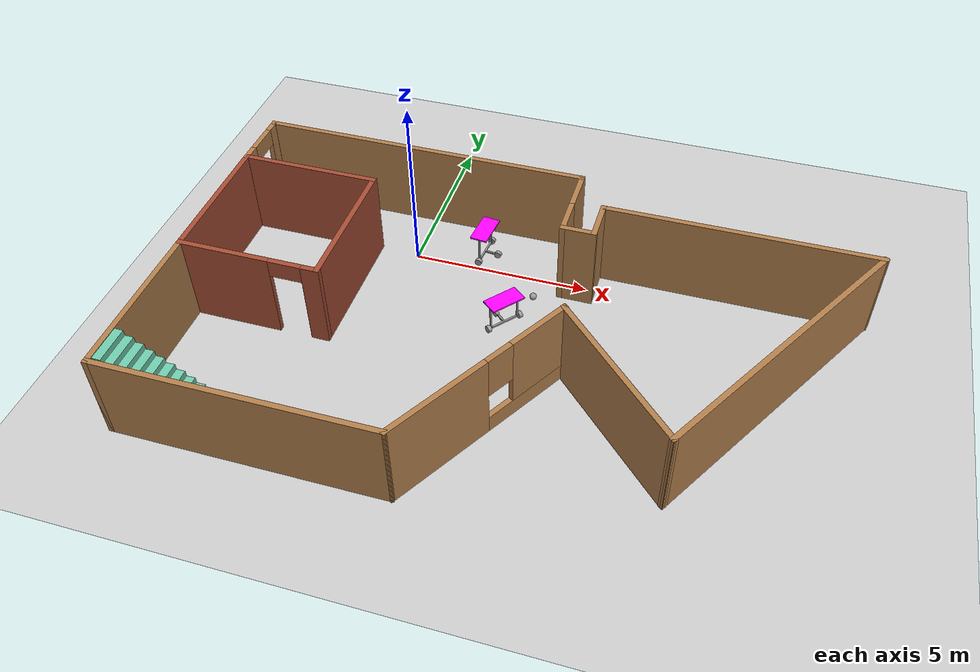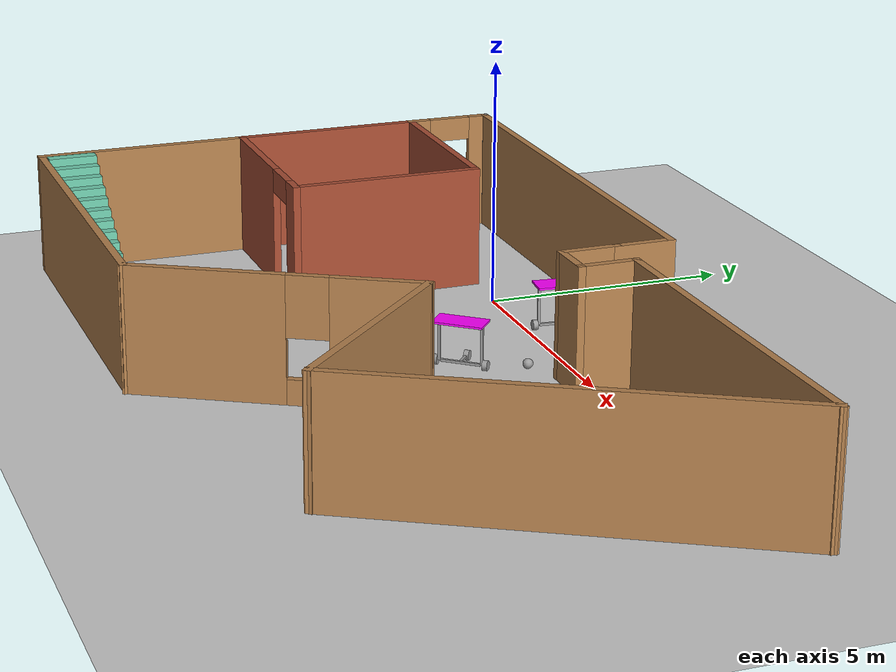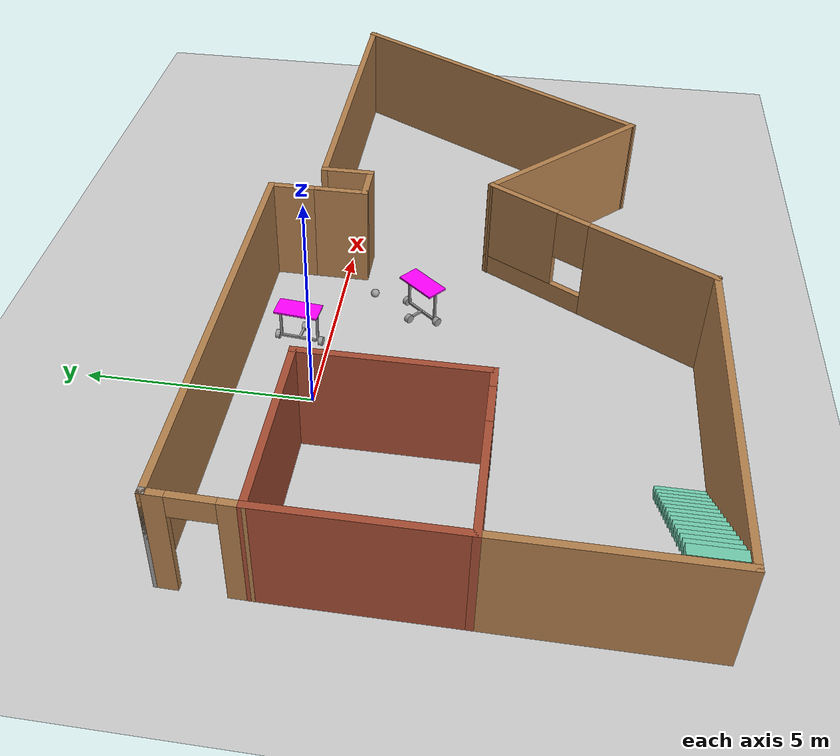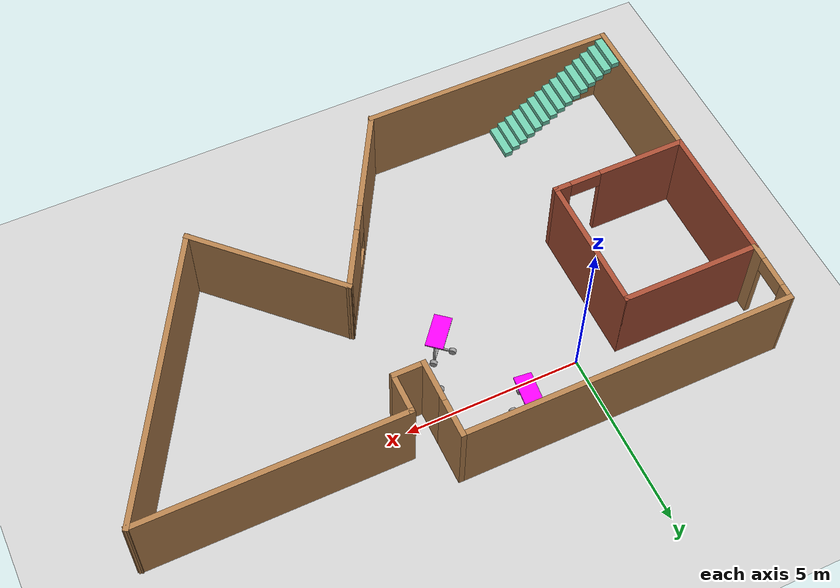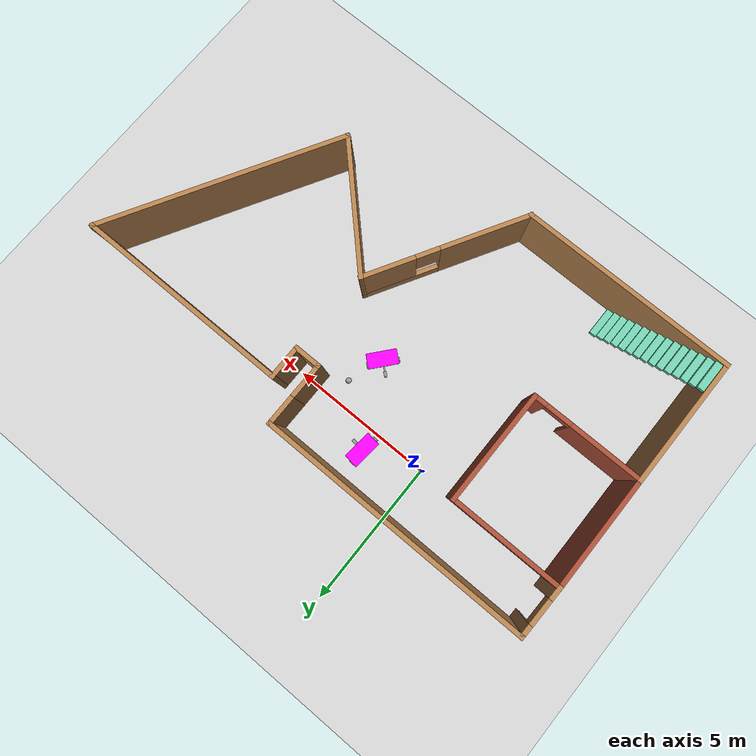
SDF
<sdf version="1.7">
 <world name="default">
  <light name="sun" type="directional">
   <pose>0 0 10 0 -0 0</pose>
   <diffuse>0.8 0.8 0.8 1</diffuse>
   <specular>0.2 0.2 0.2 1</specular>
   <attenuation>
    <range>1000</range>
    <constant>0.9</constant>
    <linear>0.01</linear>
    <quadratic>0.001</quadratic>
   </attenuation>
   <direction>-0.5 0.1 -0.9</direction>
   <spot><inner_angle>0</inner_angle><outer_angle>0</outer_angle><falloff>0</falloff></spot>
  </light>
  <model name="ground_plane">
   <static>1</static>
   <link name="link">
    <collision name="collision">
     <geometry><plane><normal>0 0 1</normal><size>100 100</size></plane></geometry>
     <surface>
      <contact><collide_bitmask>65535</collide_bitmask></contact>
      <friction><ode><mu>100</mu><mu2>50</mu2></ode></friction>
     </surface>
    </collision>
    <visual name="visual">
     <cast_shadows>0</cast_shadows>
     <geometry><plane><normal>0 0 1</normal><size>100 100</size></plane></geometry>
     <material>
      <script><uri>file://media/materials/scripts/gazebo.material</uri><name>Gazebo/Grey</name></script>
     </material>
    </visual>
   </link>
  </model>
  <gravity>0 0 -9.8</gravity>
  <magnetic_field>6e-06 2.3e-05 -4.2e-05</magnetic_field>
  <atmosphere type="adiabatic"/>
  <physics type="ode">
   <max_step_size>0.001</max_step_size>
   <real_time_factor>1</real_time_factor>
   <real_time_update_rate>1000</real_time_update_rate>
  </physics>
  <scene><ambient>0.4 0.4 0.4 1</ambient><background>0.7 0.7 0.7 1</background><shadows>1</shadows></scene>
  <spherical_coordinates>
   <surface_model>EARTH_WGS84</surface_model>
   <latitude_deg>0</latitude_deg>
   <longitude_deg>0</longitude_deg>
   <elevation>0</elevation>
   <heading_deg>0</heading_deg>
  </spherical_coordinates>
  <model name="Building">
   <pose>3.7698 -3.19808 0 0 -0 0</pose>
   <link name="Stairs_3">
    <visual name="Stairs_3_Visual_0">
     <pose>-5.32922 -4.35034 0.083333 0 -0 -1.5708</pose>
     <geometry><box><size>1 0.233333 0.166667</size></box></geometry>
     <material>
      <script><uri>file://media/materials/scripts/gazebo.material</uri><name>Gazebo/Grey</name></script>
      <ambient>0.435294 0.796078 0.67451 1</ambient>
     </material>
     <meta><layer>0</layer></meta>
    </visual>
    <collision name="Stairs_3_Collision_0">
     <geometry><box><size>1 0.233333 0.166667</size></box></geometry>
     <pose>-5.32922 -4.35034 0.083333 0 -0 -1.5708</pose>
    </collision>
    <visual name="Stairs_3_Visual_1">
     <pose>-5.56255 -4.35034 0.25 0 -0 -1.5708</pose>
     <geometry><box><size>1 0.233333 0.166667</size></box></geometry>
     <material>
      <script><uri>file://media/materials/scripts/gazebo.material</uri><name>Gazebo/Grey</name></script>
      <ambient>0.435294 0.796078 0.67451 1</ambient>
     </material>
     <meta><layer>0</layer></meta>
    </visual>
    <collision name="Stairs_3_Collision_1">
     <geometry><box><size>1 0.233333 0.166667</size></box></geometry>
     <pose>-5.56255 -4.35034 0.25 0 -0 -1.5708</pose>
    </collision>
    <visual name="Stairs_3_Visual_2">
     <pose>-5.79589 -4.35034 0.416667 0 -0 -1.5708</pose>
     <geometry><box><size>1 0.233333 0.166667</size></box></geometry>
     <material>
      <script><uri>file://media/materials/scripts/gazebo.material</uri><name>Gazebo/Grey</name></script>
      <ambient>0.435294 0.796078 0.67451 1</ambient>
     </material>
     <meta><layer>0</layer></meta>
    </visual>
    <collision name="Stairs_3_Collision_2">
     <geometry><box><size>1 0.233333 0.166667</size></box></geometry>
     <pose>-5.79589 -4.35034 0.416667 0 -0 -1.5708</pose>
    </collision>
    <visual name="Stairs_3_Visual_3">
     <pose>-6.02922 -4.35034 0.583333 0 -0 -1.5708</pose>
     <geometry><box><size>1 0.233333 0.166667</size></box></geometry>
     <material>
      <script><uri>file://media/materials/scripts/gazebo.material</uri><name>Gazebo/Grey</name></script>
      <ambient>0.435294 0.796078 0.67451 1</ambient>
     </material>
     <meta><layer>0</layer></meta>
    </visual>
    <collision name="Stairs_3_Collision_3">
     <geometry><box><size>1 0.233333 0.166667</size></box></geometry>
     <pose>-6.02922 -4.35034 0.583333 0 -0 -1.5708</pose>
    </collision>
    <visual name="Stairs_3_Visual_4">
     <pose>-6.26255 -4.35034 0.75 0 -0 -1.5708</pose>
     <geometry><box><size>1 0.233333 0.166667</size></box></geometry>
     <material>
      <script><uri>file://media/materials/scripts/gazebo.material</uri><name>Gazebo/Grey</name></script>
      <ambient>0.435294 0.796078 0.67451 1</ambient>
     </material>
     <meta><layer>0</layer></meta>
    </visual>
    <collision name="Stairs_3_Collision_4">
     <geometry><box><size>1 0.233333 0.166667</size></box></geometry>
     <pose>-6.26255 -4.35034 0.75 0 -0 -1.5708</pose>
    </collision>
    <visual name="Stairs_3_Visual_5">
     <pose>-6.49589 -4.35034 0.916667 0 -0 -1.5708</pose>
     <geometry><box><size>1 0.233333 0.166667</size></box></geometry>
     <material>
      <script><uri>file://media/materials/scripts/gazebo.material</uri><name>Gazebo/Grey</name></script>
      <ambient>0.435294 0.796078 0.67451 1</ambient>
     </material>
     <meta><layer>0</layer></meta>
    </visual>
    <collision name="Stairs_3_Collision_5">
     <geometry><box><size>1 0.233333 0.166667</size></box></geometry>
     <pose>-6.49589 -4.35034 0.916667 0 -0 -1.5708</pose>
    </collision>
    <visual name="Stairs_3_Visual_6">
     <pose>-6.72922 -4.35034 1.08333 0 -0 -1.5708</pose>
     <geometry><box><size>1 0.233333 0.166667</size></box></geometry>
     <material>
      <script><uri>file://media/materials/scripts/gazebo.material</uri><name>Gazebo/Grey</name></script>
      <ambient>0.435294 0.796078 0.67451 1</ambient>
     </material>
     <meta><layer>0</layer></meta>
    </visual>
    <collision name="Stairs_3_Collision_6">
     <geometry><box><size>1 0.233333 0.166667</size></box></geometry>
     <pose>-6.72922 -4.35034 1.08333 0 -0 -1.5708</pose>
    </collision>
    <visual name="Stairs_3_Visual_7">
     <pose>-6.96255 -4.35034 1.25 0 -0 -1.5708</pose>
     <geometry><box><size>1 0.233333 0.166667</size></box></geometry>
     <material>
      <script><uri>file://media/materials/scripts/gazebo.material</uri><name>Gazebo/Grey</name></script>
      <ambient>0.435294 0.796078 0.67451 1</ambient>
     </material>
     <meta><layer>0</layer></meta>
    </visual>
    <collision name="Stairs_3_Collision_7">
     <geometry><box><size>1 0.233333 0.166667</size></box></geometry>
     <pose>-6.96255 -4.35034 1.25 0 -0 -1.5708</pose>
    </collision>
    <visual name="Stairs_3_Visual_8">
     <pose>-7.19589 -4.35034 1.41667 0 -0 -1.5708</pose>
     <geometry><box><size>1 0.233333 0.166667</size></box></geometry>
     <material>
      <script><uri>file://media/materials/scripts/gazebo.material</uri><name>Gazebo/Grey</name></script>
      <ambient>0.435294 0.796078 0.67451 1</ambient>
     </material>
     <meta><layer>0</layer></meta>
    </visual>
    <collision name="Stairs_3_Collision_8">
     <geometry><box><size>1 0.233333 0.166667</size></box></geometry>
     <pose>-7.19589 -4.35034 1.41667 0 -0 -1.5708</pose>
    </collision>
    <visual name="Stairs_3_Visual_9">
     <pose>-7.42922 -4.35034 1.58333 0 -0 -1.5708</pose>
     <geometry><box><size>1 0.233333 0.166667</size></box></geometry>
     <material>
      <script><uri>file://media/materials/scripts/gazebo.material</uri><name>Gazebo/Grey</name></script>
      <ambient>0.435294 0.796078 0.67451 1</ambient>
     </material>
     <meta><layer>0</layer></meta>
    </visual>
    <collision name="Stairs_3_Collision_9">
     <geometry><box><size>1 0.233333 0.166667</size></box></geometry>
     <pose>-7.42922 -4.35034 1.58333 0 -0 -1.5708</pose>
    </collision>
    <visual name="Stairs_3_Visual_10">
     <pose>-7.66255 -4.35034 1.75 0 -0 -1.5708</pose>
     <geometry><box><size>1 0.233333 0.166667</size></box></geometry>
     <material>
      <script><uri>file://media/materials/scripts/gazebo.material</uri><name>Gazebo/Grey</name></script>
      <ambient>0.435294 0.796078 0.67451 1</ambient>
     </material>
     <meta><layer>0</layer></meta>
    </visual>
    <collision name="Stairs_3_Collision_10">
     <geometry><box><size>1 0.233333 0.166667</size></box></geometry>
     <pose>-7.66255 -4.35034 1.75 0 -0 -1.5708</pose>
    </collision>
    <visual name="Stairs_3_Visual_11">
     <pose>-7.89589 -4.35034 1.91667 0 -0 -1.5708</pose>
     <geometry><box><size>1 0.233333 0.166667</size></box></geometry>
     <material>
      <script><uri>file://media/materials/scripts/gazebo.material</uri><name>Gazebo/Grey</name></script>
      <ambient>0.435294 0.796078 0.67451 1</ambient>
     </material>
     <meta><layer>0</layer></meta>
    </visual>
    <collision name="Stairs_3_Collision_11">
     <geometry><box><size>1 0.233333 0.166667</size></box></geometry>
     <pose>-7.89589 -4.35034 1.91667 0 -0 -1.5708</pose>
    </collision>
    <visual name="Stairs_3_Visual_12">
     <pose>-8.12922 -4.35034 2.08333 0 -0 -1.5708</pose>
     <geometry><box><size>1 0.233333 0.166667</size></box></geometry>
     <material>
      <script><uri>file://media/materials/scripts/gazebo.material</uri><name>Gazebo/Grey</name></script>
      <ambient>0.435294 0.796078 0.67451 1</ambient>
     </material>
     <meta><layer>0</layer></meta>
    </visual>
    <collision name="Stairs_3_Collision_12">
     <geometry><box><size>1 0.233333 0.166667</size></box></geometry>
     <pose>-8.12922 -4.35034 2.08333 0 -0 -1.5708</pose>
    </collision>
    <visual name="Stairs_3_Visual_13">
     <pose>-8.36255 -4.35034 2.25 0 -0 -1.5708</pose>
     <geometry><box><size>1 0.233333 0.166667</size></box></geometry>
     <material>
      <script><uri>file://media/materials/scripts/gazebo.material</uri><name>Gazebo/Grey</name></script>
      <ambient>0.435294 0.796078 0.67451 1</ambient>
     </material>
     <meta><layer>0</layer></meta>
    </visual>
    <collision name="Stairs_3_Collision_13">
     <geometry><box><size>1 0.233333 0.166667</size></box></geometry>
     <pose>-8.36255 -4.35034 2.25 0 -0 -1.5708</pose>
    </collision>
    <visual name="Stairs_3_Visual_14">
     <pose>-8.59589 -4.35034 2.41667 0 -0 -1.5708</pose>
     <geometry><box><size>1 0.233333 0.166667</size></box></geometry>
     <material>
      <script><uri>file://media/materials/scripts/gazebo.material</uri><name>Gazebo/Grey</name></script>
      <ambient>0.435294 0.796078 0.67451 1</ambient>
     </material>
     <meta><layer>0</layer></meta>
    </visual>
    <collision name="Stairs_3_Collision_14">
     <geometry><box><size>1 0.233333 0.166667</size></box></geometry>
     <pose>-8.59589 -4.35034 2.41667 0 -0 -1.5708</pose>
    </collision>
   </link>
   <link name="Wall_0">
    <collision name="Wall_0_Collision">
     <geometry><box><size>4 0.15 2.5</size></box></geometry>
     <pose>0 0 1.25 0 -0 0</pose>
    </collision>
    <visual name="Wall_0_Visual">
     <pose>0 0 1.25 0 -0 0</pose>
     <geometry><box><size>4 0.15 2.5</size></box></geometry>
     <material>
      <script><uri>file://media/materials/scripts/gazebo.material</uri><name>Gazebo/Bricks</name></script>
      <ambient>1 1 1 1</ambient>
     </material>
     <meta><layer>0</layer></meta>
    </visual>
    <pose>-8.80198 1.32395 0 0 -0 1.5708</pose>
   </link>
   <link name="Wall_10">
    <collision name="Wall_10_Collision">
     <geometry><box><size>8.5 0.15 2.5</size></box></geometry>
     <pose>0 0 1.25 0 -0 0</pose>
    </collision>
    <visual name="Wall_10_Visual">
     <pose>0 0 1.25 0 -0 0</pose>
     <geometry><box><size>8.5 0.15 2.5</size></box></geometry>
     <material>
      <script><uri>file://media/materials/scripts/gazebo.material</uri><name>Gazebo/Wood</name></script>
      <ambient>1 1 1 1</ambient>
     </material>
     <meta><layer>0</layer></meta>
    </visual>
    <pose>6.68821 0.261655 0 0 -0 1.0472</pose>
   </link>
   <link name="Wall_11">
    <collision name="Wall_11_Collision">
     <geometry><box><size>7.5 0.15 2.5</size></box></geometry>
     <pose>0 0 1.25 0 -0 0</pose>
    </collision>
    <visual name="Wall_11_Visual">
     <pose>0 0 1.25 0 -0 0</pose>
     <geometry><box><size>7.5 0.15 2.5</size></box></geometry>
     <material>
      <script><uri>file://media/materials/scripts/gazebo.material</uri><name>Gazebo/Wood</name></script>
      <ambient>1 1 1 1</ambient>
     </material>
     <meta><layer>0</layer></meta>
    </visual>
    <pose>5.10072 3.87731 0 0 -0 3.14159</pose>
   </link>
   <link name="Wall_12">
    <collision name="Wall_12_Collision">
     <geometry><box><size>1.25 0.15 2.5</size></box></geometry>
     <pose>0 0 1.25 0 -0 0</pose>
    </collision>
    <visual name="Wall_12_Visual">
     <pose>0 0 1.25 0 -0 0</pose>
     <geometry><box><size>1.25 0.15 2.5</size></box></geometry>
     <material>
      <script><uri>file://media/materials/scripts/gazebo.material</uri><name>Gazebo/Wood</name></script>
      <ambient>1 1 1 1</ambient>
     </material>
     <meta><layer>0</layer></meta>
    </visual>
    <pose>1.42572 3.32731 0 0 -0 -1.5708</pose>
   </link>
   <link name="Wall_13">
    <collision name="Wall_13_Collision">
     <geometry><box><size>1 0.15 2.5</size></box></geometry>
     <pose>0 0 1.25 0 -0 0</pose>
    </collision>
    <visual name="Wall_13_Visual">
     <pose>0 0 1.25 0 -0 0</pose>
     <geometry><box><size>1 0.15 2.5</size></box></geometry>
     <material>
      <script><uri>file://media/materials/scripts/gazebo.material</uri><name>Gazebo/Wood</name></script>
      <ambient>1 1 1 1</ambient>
     </material>
     <meta><layer>0</layer></meta>
    </visual>
    <pose>1.00072 2.77731 0 0 -0 3.14159</pose>
   </link>
   <link name="Wall_14">
    <collision name="Wall_14_Collision">
     <geometry><box><size>1.25 0.15 2.5</size></box></geometry>
     <pose>0 0 1.25 0 -0 0</pose>
    </collision>
    <visual name="Wall_14_Visual">
     <pose>0 0 1.25 0 -0 0</pose>
     <geometry><box><size>1.25 0.15 2.5</size></box></geometry>
     <material>
      <script><uri>file://media/materials/scripts/gazebo.material</uri><name>Gazebo/Wood</name></script>
      <ambient>1 1 1 1</ambient>
     </material>
     <meta><layer>0</layer></meta>
    </visual>
    <pose>0.575715 3.32731 0 0 -0 1.5708</pose>
   </link>
   <link name="Wall_15">
    <collision name="Wall_15_Collision">
     <geometry><box><size>1.25 0.15 2.5</size></box></geometry>
     <pose>0 0 1.25 0 -0 0</pose>
    </collision>
    <visual name="Wall_15_Visual">
     <pose>0 0 1.25 0 -0 0</pose>
     <geometry><box><size>1.25 0.15 2.5</size></box></geometry>
     <material>
      <script><uri>file://media/materials/scripts/gazebo.material</uri><name>Gazebo/Wood</name></script>
      <ambient>1 1 1 1</ambient>
     </material>
     <meta><layer>0</layer></meta>
    </visual>
    <pose>0.575715 4.42731 0 0 -0 1.5708</pose>
   </link>
   <link name="Wall_16">
    <collision name="Wall_16_Collision">
     <geometry><box><size>9.5 0.15 2.5</size></box></geometry>
     <pose>0 0 1.25 0 -0 0</pose>
    </collision>
    <visual name="Wall_16_Visual">
     <pose>0 0 1.25 0 -0 0</pose>
     <geometry><box><size>9.5 0.15 2.5</size></box></geometry>
     <material>
      <script><uri>file://media/materials/scripts/gazebo.material</uri><name>Gazebo/Wood</name></script>
      <ambient>1 1 1 1</ambient>
     </material>
     <meta><layer>0</layer></meta>
    </visual>
    <pose>-4.09929 4.97731 0 0 -0 3.14159</pose>
   </link>
   <link name="Wall_18">
    <collision name="Wall_18_Collision">
     <geometry><box><size>0.15 0.15 2.5</size></box></geometry>
     <pose>0 0 1.25 0 -0 0</pose>
    </collision>
    <visual name="Wall_18_Visual">
     <pose>0 0 1.25 0 -0 0</pose>
     <geometry><box><size>0.15 0.15 2.5</size></box></geometry>
     <material>
      <script><uri>file://media/materials/scripts/gazebo.material</uri><name>Gazebo/Grey</name></script>
      <ambient>1 1 1 1</ambient>
     </material>
     <meta><layer>0</layer></meta>
    </visual>
    <pose>-8.77429 4.97731 0 0 -0 0</pose>
   </link>
   <link name="Wall_2">
    <collision name="Wall_2_Collision">
     <geometry><box><size>4 0.15 2.5</size></box></geometry>
     <pose>0 0 1.25 0 -0 0</pose>
    </collision>
    <visual name="Wall_2_Visual">
     <pose>0 0 1.25 0 -0 0</pose>
     <geometry><box><size>4 0.15 2.5</size></box></geometry>
     <material>
      <script><uri>file://media/materials/scripts/gazebo.material</uri><name>Gazebo/Bricks</name></script>
      <ambient>1 1 1 1</ambient>
     </material>
     <meta><layer>0</layer></meta>
    </visual>
    <pose>-6.87698 3.24895 0 0 -0 0</pose>
   </link>
   <link name="Wall_3">
    <collision name="Wall_3_Collision">
     <geometry><box><size>4 0.15 2.5</size></box></geometry>
     <pose>0 0 1.25 0 -0 0</pose>
    </collision>
    <visual name="Wall_3_Visual">
     <pose>0 0 1.25 0 -0 0</pose>
     <geometry><box><size>4 0.15 2.5</size></box></geometry>
     <material>
      <script><uri>file://media/materials/scripts/gazebo.material</uri><name>Gazebo/Bricks</name></script>
      <ambient>1 1 1 1</ambient>
     </material>
     <meta><layer>0</layer></meta>
    </visual>
    <pose>-4.95198 1.32395 0 0 -0 -1.5708</pose>
   </link>
   <link name="Wall_36">
    <pose>-8.78813 4.11313 0 0 -0 -1.58682</pose>
    <visual name="Wall_36_Visual_0">
     <pose>-0.702164 0 1.25 0 -0 0</pose>
     <geometry><box><size>0.474256 0.15 2.5</size></box></geometry>
     <material>
      <script><uri>file://media/materials/scripts/gazebo.material</uri><name>Gazebo/Wood</name></script>
      <ambient>1 1 1 1</ambient>
     </material>
     <meta><layer>0</layer></meta>
    </visual>
    <collision name="Wall_36_Collision_0">
     <geometry><box><size>0.474256 0.15 2.5</size></box></geometry>
     <pose>-0.702164 0 1.25 0 -0 0</pose>
    </collision>
    <visual name="Wall_36_Visual_1">
     <pose>0.687128 0 1.25 0 -0 0</pose>
     <geometry><box><size>0.504329 0.15 2.5</size></box></geometry>
     <material>
      <script><uri>file://media/materials/scripts/gazebo.material</uri><name>Gazebo/Wood</name></script>
      <ambient>1 1 1 1</ambient>
     </material>
     <meta><layer>0</layer></meta>
    </visual>
    <collision name="Wall_36_Collision_1">
     <geometry><box><size>0.504329 0.15 2.5</size></box></geometry>
     <pose>0.687128 0 1.25 0 -0 0</pose>
    </collision>
    <visual name="Wall_36_Visual_2">
     <pose>-0.015036 0 2.25 0 -0 0</pose>
     <geometry><box><size>0.9 0.15 0.5</size></box></geometry>
     <material>
      <script><uri>file://media/materials/scripts/gazebo.material</uri><name>Gazebo/Wood</name></script>
      <ambient>1 1 1 1</ambient>
     </material>
     <meta><layer>0</layer></meta>
    </visual>
    <collision name="Wall_36_Collision_2">
     <geometry><box><size>0.9 0.15 0.5</size></box></geometry>
     <pose>-0.015036 0 2.25 0 -0 0</pose>
    </collision>
   </link>
   <link name="Wall_38">
    <pose>-6.87698 -0.601052 0 0 -0 3.14159</pose>
    <visual name="Wall_38_Visual_0">
     <pose>-1.74342 0 1.25 0 -0 0</pose>
     <geometry><box><size>0.513155 0.15 2.5</size></box></geometry>
     <material>
      <script><uri>file://media/materials/scripts/gazebo.material</uri><name>Gazebo/Bricks</name></script>
      <ambient>1 1 1 1</ambient>
     </material>
     <meta><layer>0</layer></meta>
    </visual>
    <collision name="Wall_38_Collision_0">
     <geometry><box><size>0.513155 0.15 2.5</size></box></geometry>
     <pose>-1.74342 0 1.25 0 -0 0</pose>
    </collision>
    <visual name="Wall_38_Visual_1">
     <pose>0.706577 0 1.25 0 -0 0</pose>
     <geometry><box><size>2.58684 0.15 2.5</size></box></geometry>
     <material>
      <script><uri>file://media/materials/scripts/gazebo.material</uri><name>Gazebo/Bricks</name></script>
      <ambient>1 1 1 1</ambient>
     </material>
     <meta><layer>0</layer></meta>
    </visual>
    <collision name="Wall_38_Collision_1">
     <geometry><box><size>2.58684 0.15 2.5</size></box></geometry>
     <pose>0.706577 0 1.25 0 -0 0</pose>
    </collision>
    <visual name="Wall_38_Visual_2">
     <pose>-1.03685 0 2.25 0 -0 0</pose>
     <geometry><box><size>0.9 0.15 0.5</size></box></geometry>
     <material>
      <script><uri>file://media/materials/scripts/gazebo.material</uri><name>Gazebo/Bricks</name></script>
      <ambient>1 1 1 1</ambient>
     </material>
     <meta><layer>0</layer></meta>
    </visual>
    <collision name="Wall_38_Collision_2">
     <geometry><box><size>0.9 0.15 0.5</size></box></geometry>
     <pose>-1.03685 0 2.25 0 -0 0</pose>
    </collision>
   </link>
   <link name="Wall_6">
    <collision name="Wall_6_Collision">
     <geometry><box><size>4.5 0.15 2.5</size></box></geometry>
     <pose>0 0 1.25 0 -0 0</pose>
    </collision>
    <visual name="Wall_6_Visual">
     <pose>0 0 1.25 0 -0 0</pose>
     <geometry><box><size>4.5 0.15 2.5</size></box></geometry>
     <material>
      <script><uri>file://media/materials/scripts/gazebo.material</uri><name>Gazebo/Wood</name></script>
      <ambient>1 1 1 1</ambient>
     </material>
     <meta><layer>0</layer></meta>
    </visual>
    <pose>-8.80198 -2.77605 0 0 -0 -1.5708</pose>
   </link>
   <link name="Wall_7">
    <collision name="Wall_7_Collision">
     <geometry><box><size>7.5 0.15 2.5</size></box></geometry>
     <pose>0 0 1.25 0 -0 0</pose>
    </collision>
    <visual name="Wall_7_Visual">
     <pose>0 0 1.25 0 -0 0</pose>
     <geometry><box><size>7.5 0.15 2.5</size></box></geometry>
     <material>
      <script><uri>file://media/materials/scripts/gazebo.material</uri><name>Gazebo/Wood</name></script>
      <ambient>1 1 1 1</ambient>
     </material>
     <meta><layer>0</layer></meta>
    </visual>
    <pose>-5.12698 -4.95105 0 0 -0 0</pose>
   </link>
   <link name="Wall_8">
    <pose>-0.051976 -2.52618 0 0 -0 1.0472</pose>
    <visual name="Wall_8_Visual_0">
     <pose>-1.33048 0 1.25 0 -0 0</pose>
     <geometry><box><size>3.08904 0.15 2.5</size></box></geometry>
     <material>
      <script><uri>file://media/materials/scripts/gazebo.material</uri><name>Gazebo/Wood</name></script>
      <ambient>1 1 1 1</ambient>
     </material>
     <meta><layer>0</layer></meta>
    </visual>
    <collision name="Wall_8_Collision_0">
     <geometry><box><size>3.08904 0.15 2.5</size></box></geometry>
     <pose>-1.33048 0 1.25 0 -0 0</pose>
    </collision>
    <visual name="Wall_8_Visual_1">
     <pose>1.54452 0 0.25 0 -0 0</pose>
     <geometry><box><size>2.66096 0.15 0.5</size></box></geometry>
     <material>
      <script><uri>file://media/materials/scripts/gazebo.material</uri><name>Gazebo/Wood</name></script>
      <ambient>1 1 1 1</ambient>
     </material>
     <meta><layer>0</layer></meta>
    </visual>
    <collision name="Wall_8_Collision_1">
     <geometry><box><size>2.66096 0.15 0.5</size></box></geometry>
     <pose>1.54452 0 0.25 0 -0 0</pose>
    </collision>
    <visual name="Wall_8_Visual_2">
     <pose>1.94452 0 1.5 0 -0 0</pose>
     <geometry><box><size>1.86096 0.15 2</size></box></geometry>
     <material>
      <script><uri>file://media/materials/scripts/gazebo.material</uri><name>Gazebo/Wood</name></script>
      <ambient>1 1 1 1</ambient>
     </material>
     <meta><layer>0</layer></meta>
    </visual>
    <collision name="Wall_8_Collision_2">
     <geometry><box><size>1.86096 0.15 2</size></box></geometry>
     <pose>1.94452 0 1.5 0 -0 0</pose>
    </collision>
    <visual name="Wall_8_Visual_3">
     <pose>0.614037 0 1.9 0 -0 0</pose>
     <geometry><box><size>0.8 0.15 1.2</size></box></geometry>
     <material>
      <script><uri>file://media/materials/scripts/gazebo.material</uri><name>Gazebo/Wood</name></script>
      <ambient>1 1 1 1</ambient>
     </material>
     <meta><layer>0</layer></meta>
    </visual>
    <collision name="Wall_8_Collision_3">
     <geometry><box><size>0.8 0.15 1.2</size></box></geometry>
     <pose>0.614037 0 1.9 0 -0 0</pose>
    </collision>
   </link>
   <link name="Wall_9">
    <collision name="Wall_9_Collision">
     <geometry><box><size>4.75 0.15 2.5</size></box></geometry>
     <pose>0 0 1.25 0 -0 0</pose>
    </collision>
    <visual name="Wall_9_Visual">
     <pose>0 0 1.25 0 -0 0</pose>
     <geometry><box><size>4.75 0.15 2.5</size></box></geometry>
     <material>
      <script><uri>file://media/materials/scripts/gazebo.material</uri><name>Gazebo/Wood</name></script>
      <ambient>1 1 1 1</ambient>
     </material>
     <meta><layer>0</layer></meta>
    </visual>
    <pose>2.97437 -1.72765 0 0 -0 -0.785398</pose>
   </link>
   <static>1</static>
  </model>
  <model name="HumanoidRobot_3">
   <link name="link_0">
    <inertial>
     <mass>1</mass>
     <inertia>
      <ixx>0.166667</ixx>
      <ixy>0</ixy>
      <ixz>0</ixz>
      <iyy>0.166667</iyy>
      <iyz>0</iyz>
      <izz>0.166667</izz>
     </inertia>
    </inertial>
    <pose>0 -0 0.92 0 -0 0</pose>
    <visual name="visual">
     <geometry><box><size>0.5 1 0.04</size></box></geometry>
     <material>
      <lighting>1</lighting>
      <script><uri>file://media/materials/scripts/gazebo.material</uri><name>Gazebo/Grey</name></script>
      <shader type="pixel"><normal_map>__default__</normal_map></shader>
      <ambient>0.3 0.3 0.3 1</ambient>
      <diffuse>1 0 1 1</diffuse>
      <specular>0.01 0.01 0.01 1</specular>
      <emissive>0 0 0 1</emissive>
     </material>
    </visual>
    <collision name="collision">
     <geometry><box><size>0.5 1 0.04</size></box></geometry>
     <surface>
      <friction>
       <ode><mu>1</mu><mu2>1</mu2><fdir1>0 0 0</fdir1><slip1>0</slip1><slip2>0</slip2></ode>
       <torsional>
        <coefficient>1</coefficient>
        <patch_radius>0</patch_radius>
        <surface_radius>0</surface_radius>
        <use_patch_radius>1</use_patch_radius>
        <ode><slip>0</slip></ode>
       </torsional>
      </friction>
      <bounce><restitution_coefficient>0</restitution_coefficient><threshold>1e+06</threshold></bounce>
      <contact>
       <collide_without_contact>0</collide_without_contact>
       <collide_without_contact_bitmask>1</collide_without_contact_bitmask>
       <collide_bitmask>1</collide_bitmask>
       <ode>
        <soft_cfm>0</soft_cfm>
        <soft_erp>0.2</soft_erp>
        <kp>1e+13</kp>
        <kd>1</kd>
        <max_vel>0.01</max_vel>
        <min_depth>0</min_depth>
       </ode>
       <bullet>
        <split_impulse>1</split_impulse>
        <split_impulse_penetration_threshold>-0.01</split_impulse_penetration_threshold>
        <soft_cfm>0</soft_cfm>
        <soft_erp>0.2</soft_erp>
        <kp>1e+13</kp>
        <kd>1</kd>
       </bullet>
      </contact>
     </surface>
    </collision>
   </link>
   <link name="link_0_0">
    <inertial>
     <mass>1</mass>
     <inertia><ixx>0.145833</ixx><ixy>0</ixy><ixz>0</ixz><iyy>0.145833</iyy><iyz>0</iyz><izz>0.125</izz></inertia>
    </inertial>
    <pose>0 -0.5 0.1 0 -0 0</pose>
    <visual name="visual">
     <pose>0 0 0 1.5708 -0 0</pose>
     <geometry><cylinder><radius>0.1</radius><length>0.1</length></cylinder></geometry>
     <material>
      <lighting>1</lighting>
      <script><uri>file://media/materials/scripts/gazebo.material</uri><name>Gazebo/Grey</name></script>
      <shader type="pixel"><normal_map>__default__</normal_map></shader>
      <ambient>0 0 0 1</ambient>
      <diffuse>0 0 0 1</diffuse>
      <specular>0.01 0.01 0.01 1</specular>
      <emissive>0 0 0 1</emissive>
     </material>
    </visual>
    <collision name="collision">
     <pose>0 0 0 1.5708 -0 0</pose>
     <geometry><cylinder><radius>0.1</radius><length>0.1</length></cylinder></geometry>
     <surface>
      <friction>
       <ode><mu>1</mu><mu2>1</mu2><fdir1>0 0 0</fdir1><slip1>0</slip1><slip2>0</slip2></ode>
       <torsional>
        <coefficient>1</coefficient>
        <patch_radius>0</patch_radius>
        <surface_radius>0</surface_radius>
        <use_patch_radius>1</use_patch_radius>
        <ode><slip>0</slip></ode>
       </torsional>
      </friction>
      <bounce><restitution_coefficient>0</restitution_coefficient><threshold>1e+06</threshold></bounce>
      <contact>
       <collide_without_contact>0</collide_without_contact>
       <collide_without_contact_bitmask>1</collide_without_contact_bitmask>
       <collide_bitmask>1</collide_bitmask>
       <ode>
        <soft_cfm>0</soft_cfm>
        <soft_erp>0.2</soft_erp>
        <kp>1e+13</kp>
        <kd>1</kd>
        <max_vel>0.01</max_vel>
        <min_depth>0</min_depth>
       </ode>
       <bullet>
        <split_impulse>1</split_impulse>
        <split_impulse_penetration_threshold>-0.01</split_impulse_penetration_threshold>
        <soft_cfm>0</soft_cfm>
        <soft_erp>0.2</soft_erp>
        <kp>1e+13</kp>
        <kd>1</kd>
       </bullet>
      </contact>
     </surface>
    </collision>
   </link>
   <link name="link_0_0_clone">
    <inertial>
     <mass>1</mass>
     <inertia><ixx>0.145833</ixx><ixy>0</ixy><ixz>0</ixz><iyy>0.145833</iyy><iyz>0</iyz><izz>0.125</izz></inertia>
    </inertial>
    <pose>-0 0.5 0.1 0 -0 0</pose>
    <visual name="visual_0">
     <pose>0 0 0 1.5708 -0 0</pose>
     <geometry><cylinder><radius>0.1</radius><length>0.1</length></cylinder></geometry>
     <material>
      <lighting>1</lighting>
      <script><uri>file://media/materials/scripts/gazebo.material</uri><name>Gazebo/Gray</name></script>
      <shader type="pixel"><normal_map>__default__</normal_map></shader>
      <ambient>0 0 0 1</ambient>
      <diffuse>0 0 0 1</diffuse>
      <specular>0.01 0.01 0.01 1</specular>
      <emissive>0 0 0 1</emissive>
     </material>
    </visual>
    <collision name="collision">
     <pose>0 0 0 1.5708 -0 0</pose>
     <geometry><cylinder><radius>0.1</radius><length>0.1</length></cylinder></geometry>
     <surface>
      <friction>
       <ode><mu>1</mu><mu2>1</mu2><fdir1>0 0 0</fdir1><slip1>0</slip1><slip2>0</slip2></ode>
       <torsional>
        <coefficient>1</coefficient>
        <patch_radius>0</patch_radius>
        <surface_radius>0</surface_radius>
        <use_patch_radius>1</use_patch_radius>
        <ode><slip>0</slip></ode>
       </torsional>
      </friction>
      <bounce><restitution_coefficient>0</restitution_coefficient><threshold>1e+06</threshold></bounce>
      <contact>
       <collide_without_contact>0</collide_without_contact>
       <collide_without_contact_bitmask>1</collide_without_contact_bitmask>
       <collide_bitmask>1</collide_bitmask>
       <ode>
        <soft_cfm>0</soft_cfm>
        <soft_erp>0.2</soft_erp>
        <kp>1e+13</kp>
        <kd>1</kd>
        <max_vel>0.01</max_vel>
        <min_depth>0</min_depth>
       </ode>
       <bullet>
        <split_impulse>1</split_impulse>
        <split_impulse_penetration_threshold>-0.01</split_impulse_penetration_threshold>
        <soft_cfm>0</soft_cfm>
        <soft_erp>0.2</soft_erp>
        <kp>1e+13</kp>
        <kd>1</kd>
       </bullet>
      </contact>
     </surface>
    </collision>
   </link>
   <link name="link_0_0_clone_0">
    <inertial>
     <mass>1</mass>
     <inertia><ixx>0.145833</ixx><ixy>0</ixy><ixz>0</ixz><iyy>0.145833</iyy><iyz>0</iyz><izz>0.125</izz></inertia>
    </inertial>
    <pose>0.4 0 0.1 0 -0 0</pose>
    <visual name="visual">
     <pose>0 0 0 1.5708 -0 0</pose>
     <geometry><cylinder><radius>0.1</radius><length>0.1</length></cylinder></geometry>
     <material>
      <lighting>1</lighting>
      <script><uri>file://media/materials/scripts/gazebo.material</uri><name>Gazebo/Grey</name></script>
      <shader type="pixel"><normal_map>__default__</normal_map></shader>
      <ambient>0 0 0 1</ambient>
      <diffuse>0 0 0 1</diffuse>
      <specular>0.01 0.01 0.01 1</specular>
      <emissive>0 0 0 1</emissive>
     </material>
    </visual>
    <collision name="collision">
     <pose>0 0 0 1.5708 -0 0</pose>
     <geometry><cylinder><radius>0.1</radius><length>0.1</length></cylinder></geometry>
     <surface>
      <friction>
       <ode><mu>1</mu><mu2>1</mu2><fdir1>0 0 0</fdir1><slip1>0</slip1><slip2>0</slip2></ode>
       <torsional>
        <coefficient>1</coefficient>
        <patch_radius>0</patch_radius>
        <surface_radius>0</surface_radius>
        <use_patch_radius>1</use_patch_radius>
        <ode><slip>0</slip></ode>
       </torsional>
      </friction>
      <bounce><restitution_coefficient>0</restitution_coefficient><threshold>1e+06</threshold></bounce>
      <contact>
       <collide_without_contact>0</collide_without_contact>
       <collide_without_contact_bitmask>1</collide_without_contact_bitmask>
       <collide_bitmask>1</collide_bitmask>
       <ode>
        <soft_cfm>0</soft_cfm>
        <soft_erp>0.2</soft_erp>
        <kp>1e+13</kp>
        <kd>1</kd>
        <max_vel>0.01</max_vel>
        <min_depth>0</min_depth>
       </ode>
       <bullet>
        <split_impulse>1</split_impulse>
        <split_impulse_penetration_threshold>-0.01</split_impulse_penetration_threshold>
        <soft_cfm>0</soft_cfm>
        <soft_erp>0.2</soft_erp>
        <kp>1e+13</kp>
        <kd>1</kd>
       </bullet>
      </contact>
     </surface>
    </collision>
   </link>
   <link name="link_1">
    <inertial>
     <mass>1</mass>
     <inertia>
      <ixx>0.166667</ixx>
      <ixy>0</ixy>
      <ixz>0</ixz>
      <iyy>0.166667</iyy>
      <iyz>0</iyz>
      <izz>0.166667</izz>
     </inertia>
    </inertial>
    <pose>0 -0.425 0.5 0 -0 0</pose>
    <visual name="visual">
     <geometry><box><size>0.05 0.05 0.8</size></box></geometry>
     <material>
      <lighting>1</lighting>
      <script><uri>file://media/materials/scripts/gazebo.material</uri><name>Gazebo/Grey</name></script>
      <shader type="pixel"><normal_map>__default__</normal_map></shader>
      <ambient>0.3 0.3 0.3 1</ambient>
      <diffuse>0.7 0.7 0.7 1</diffuse>
      <specular>0.01 0.01 0.01 1</specular>
      <emissive>0 0 0 1</emissive>
     </material>
    </visual>
    <collision name="collision">
     <geometry><box><size>0.05 0.05 0.8</size></box></geometry>
     <surface>
      <friction>
       <ode><mu>1</mu><mu2>1</mu2><fdir1>0 0 0</fdir1><slip1>0</slip1><slip2>0</slip2></ode>
       <torsional>
        <coefficient>1</coefficient>
        <patch_radius>0</patch_radius>
        <surface_radius>0</surface_radius>
        <use_patch_radius>1</use_patch_radius>
        <ode><slip>0</slip></ode>
       </torsional>
      </friction>
      <bounce><restitution_coefficient>0</restitution_coefficient><threshold>1e+06</threshold></bounce>
      <contact>
       <collide_without_contact>0</collide_without_contact>
       <collide_without_contact_bitmask>1</collide_without_contact_bitmask>
       <collide_bitmask>1</collide_bitmask>
       <ode>
        <soft_cfm>0</soft_cfm>
        <soft_erp>0.2</soft_erp>
        <kp>1e+13</kp>
        <kd>1</kd>
        <max_vel>0.01</max_vel>
        <min_depth>0</min_depth>
       </ode>
       <bullet>
        <split_impulse>1</split_impulse>
        <split_impulse_penetration_threshold>-0.01</split_impulse_penetration_threshold>
        <soft_cfm>0</soft_cfm>
        <soft_erp>0.2</soft_erp>
        <kp>1e+13</kp>
        <kd>1</kd>
       </bullet>
      </contact>
     </surface>
    </collision>
   </link>
   <link name="link_1_clone">
    <inertial>
     <mass>1</mass>
     <inertia>
      <ixx>0.166667</ixx>
      <ixy>0</ixy>
      <ixz>0</ixz>
      <iyy>0.166667</iyy>
      <iyz>0</iyz>
      <izz>0.166667</izz>
     </inertia>
    </inertial>
    <pose>0 0.425 0.5 0 -0 0</pose>
    <visual name="visual">
     <geometry><box><size>0.05 0.05 0.8</size></box></geometry>
     <material>
      <lighting>1</lighting>
      <script><uri>file://media/materials/scripts/gazebo.material</uri><name>Gazebo/Grey</name></script>
      <shader type="pixel"><normal_map>__default__</normal_map></shader>
      <ambient>0.3 0.3 0.3 1</ambient>
      <diffuse>0.7 0.7 0.7 1</diffuse>
      <specular>0.01 0.01 0.01 1</specular>
      <emissive>0 0 0 1</emissive>
     </material>
    </visual>
    <collision name="collision">
     <geometry><box><size>0.05 0.05 0.8</size></box></geometry>
     <surface>
      <friction>
       <ode><mu>1</mu><mu2>1</mu2><fdir1>0 0 0</fdir1><slip1>0</slip1><slip2>0</slip2></ode>
       <torsional>
        <coefficient>1</coefficient>
        <patch_radius>0</patch_radius>
        <surface_radius>0</surface_radius>
        <use_patch_radius>1</use_patch_radius>
        <ode><slip>0</slip></ode>
       </torsional>
      </friction>
      <bounce><restitution_coefficient>0</restitution_coefficient><threshold>1e+06</threshold></bounce>
      <contact>
       <collide_without_contact>0</collide_without_contact>
       <collide_without_contact_bitmask>1</collide_without_contact_bitmask>
       <collide_bitmask>1</collide_bitmask>
       <ode>
        <soft_cfm>0</soft_cfm>
        <soft_erp>0.2</soft_erp>
        <kp>1e+13</kp>
        <kd>1</kd>
        <max_vel>0.01</max_vel>
        <min_depth>0</min_depth>
       </ode>
       <bullet>
        <split_impulse>1</split_impulse>
        <split_impulse_penetration_threshold>-0.01</split_impulse_penetration_threshold>
        <soft_cfm>0</soft_cfm>
        <soft_erp>0.2</soft_erp>
        <kp>1e+13</kp>
        <kd>1</kd>
       </bullet>
      </contact>
     </surface>
    </collision>
   </link>
   <link name="link_1_clone_0">
    <inertial>
     <mass>1</mass>
     <inertia>
      <ixx>0.166667</ixx>
      <ixy>0</ixy>
      <ixz>0</ixz>
      <iyy>0.166667</iyy>
      <iyz>0</iyz>
      <izz>0.166667</izz>
     </inertia>
    </inertial>
    <pose>0 0 0.1 0 -0 0</pose>
    <visual name="visual">
     <geometry><box><size>0.05 0.8 0.05</size></box></geometry>
     <material>
      <lighting>1</lighting>
      <script><uri>file://media/materials/scripts/gazebo.material</uri><name>Gazebo/Grey</name></script>
      <shader type="pixel"><normal_map>__default__</normal_map></shader>
      <ambient>0.3 0.3 0.3 1</ambient>
      <diffuse>0.7 0.7 0.7 1</diffuse>
      <specular>0.01 0.01 0.01 1</specular>
      <emissive>0 0 0 1</emissive>
     </material>
    </visual>
    <collision name="collision">
     <geometry><box><size>0.05 0.8 0.05</size></box></geometry>
     <surface>
      <friction>
       <ode><mu>1</mu><mu2>1</mu2><fdir1>0 0 0</fdir1><slip1>0</slip1><slip2>0</slip2></ode>
       <torsional>
        <coefficient>1</coefficient>
        <patch_radius>0</patch_radius>
        <surface_radius>0</surface_radius>
        <use_patch_radius>1</use_patch_radius>
        <ode><slip>0</slip></ode>
       </torsional>
      </friction>
      <bounce><restitution_coefficient>0</restitution_coefficient><threshold>1e+06</threshold></bounce>
      <contact>
       <collide_without_contact>0</collide_without_contact>
       <collide_without_contact_bitmask>1</collide_without_contact_bitmask>
       <collide_bitmask>1</collide_bitmask>
       <ode>
        <soft_cfm>0</soft_cfm>
        <soft_erp>0.2</soft_erp>
        <kp>1e+13</kp>
        <kd>1</kd>
        <max_vel>0.01</max_vel>
        <min_depth>0</min_depth>
       </ode>
       <bullet>
        <split_impulse>1</split_impulse>
        <split_impulse_penetration_threshold>-0.01</split_impulse_penetration_threshold>
        <soft_cfm>0</soft_cfm>
        <soft_erp>0.2</soft_erp>
        <kp>1e+13</kp>
        <kd>1</kd>
       </bullet>
      </contact>
     </surface>
    </collision>
   </link>
   <link name="link_1_clone_0_clone">
    <inertial>
     <mass>1</mass>
     <inertia>
      <ixx>0.166667</ixx>
      <ixy>0</ixy>
      <ixz>0</ixz>
      <iyy>0.166667</iyy>
      <iyz>0</iyz>
      <izz>0.166667</izz>
     </inertia>
    </inertial>
    <pose>0.2 -0 0.1 0 -0 0</pose>
    <visual name="visual">
     <geometry><box><size>0.4 0.05 0.05</size></box></geometry>
     <material>
      <lighting>1</lighting>
      <script><uri>file://media/materials/scripts/gazebo.material</uri><name>Gazebo/Grey</name></script>
      <shader type="pixel"><normal_map>__default__</normal_map></shader>
      <ambient>0.3 0.3 0.3 1</ambient>
      <diffuse>0.7 0.7 0.7 1</diffuse>
      <specular>0.01 0.01 0.01 1</specular>
      <emissive>0 0 0 1</emissive>
     </material>
    </visual>
    <collision name="collision">
     <geometry><box><size>0.4 0.05 0.05</size></box></geometry>
     <surface>
      <friction>
       <ode><mu>1</mu><mu2>1</mu2><fdir1>0 0 0</fdir1><slip1>0</slip1><slip2>0</slip2></ode>
       <torsional>
        <coefficient>1</coefficient>
        <patch_radius>0</patch_radius>
        <surface_radius>0</surface_radius>
        <use_patch_radius>1</use_patch_radius>
        <ode><slip>0</slip></ode>
       </torsional>
      </friction>
      <bounce><restitution_coefficient>0</restitution_coefficient><threshold>1e+06</threshold></bounce>
      <contact>
       <collide_without_contact>0</collide_without_contact>
       <collide_without_contact_bitmask>1</collide_without_contact_bitmask>
       <collide_bitmask>1</collide_bitmask>
       <ode>
        <soft_cfm>0</soft_cfm>
        <soft_erp>0.2</soft_erp>
        <kp>1e+13</kp>
        <kd>1</kd>
        <max_vel>0.01</max_vel>
        <min_depth>0</min_depth>
       </ode>
       <bullet>
        <split_impulse>1</split_impulse>
        <split_impulse_penetration_threshold>-0.01</split_impulse_penetration_threshold>
        <soft_cfm>0</soft_cfm>
        <soft_erp>0.2</soft_erp>
        <kp>1e+13</kp>
        <kd>1</kd>
       </bullet>
      </contact>
     </surface>
    </collision>
   </link>
   <joint name="link_0_JOINT_1" type="fixed">
    <parent>link_0</parent>
    <child>link_1</child>
    <physics>
     <ode><limit><cfm>0</cfm><erp>0.2</erp></limit><suspension><cfm>0</cfm><erp>0.2</erp></suspension></ode>
    </physics>
   </joint>
   <joint name="link_0_JOINT_2" type="fixed">
    <parent>link_0</parent>
    <child>link_1_clone</child>
    <physics>
     <ode><limit><cfm>0</cfm><erp>0.2</erp></limit><suspension><cfm>0</cfm><erp>0.2</erp></suspension></ode>
    </physics>
   </joint>
   <joint name="link_1_JOINT_0" type="revolute">
    <parent>link_1</parent>
    <child>link_0_0</child>
    <axis>
     <xyz>0 1 0</xyz>
     <limit>
      <lower>-1.79769e+308</lower>
      <upper>1.79769e+308</upper>
      <effort>-1</effort>
      <velocity>-1</velocity>
     </limit>
     <dynamics>
      <spring_reference>0</spring_reference>
      <spring_stiffness>0</spring_stiffness>
      <damping>0</damping>
      <friction>0</friction>
     </dynamics>
    </axis>
    <physics>
     <ode><limit><cfm>0</cfm><erp>0.2</erp></limit><suspension><cfm>0</cfm><erp>0.2</erp></suspension></ode>
    </physics>
   </joint>
   <joint name="link_1_JOINT_6" type="fixed">
    <parent>link_1</parent>
    <child>link_1_clone_0</child>
    <physics>
     <ode><limit><cfm>0</cfm><erp>0.2</erp></limit><suspension><cfm>0</cfm><erp>0.2</erp></suspension></ode>
    </physics>
   </joint>
   <joint name="link_1_clone_0_JOINT_5" type="fixed">
    <parent>link_1_clone_0</parent>
    <child>link_1_clone_0_clone</child>
    <physics>
     <ode><limit><cfm>0</cfm><erp>0.2</erp></limit><suspension><cfm>0</cfm><erp>0.2</erp></suspension></ode>
    </physics>
   </joint>
   <joint name="link_1_clone_0_clone_JOINT_4" type="revolute">
    <parent>link_1_clone_0_clone</parent>
    <child>link_0_0_clone_0</child>
    <axis>
     <xyz>0 1 0</xyz>
     <limit>
      <lower>-1.79769e+308</lower>
      <upper>1.79769e+308</upper>
      <effort>-1</effort>
      <velocity>-1</velocity>
     </limit>
     <dynamics>
      <spring_reference>0</spring_reference>
      <spring_stiffness>0</spring_stiffness>
      <damping>0</damping>
      <friction>0</friction>
     </dynamics>
    </axis>
    <physics>
     <ode><limit><cfm>0</cfm><erp>0.2</erp></limit><suspension><cfm>0</cfm><erp>0.2</erp></suspension></ode>
    </physics>
   </joint>
   <joint name="link_1_clone_JOINT_3" type="revolute">
    <parent>link_1_clone</parent>
    <child>link_0_0_clone</child>
    <axis>
     <xyz>0 1 0</xyz>
     <limit>
      <lower>-1.79769e+308</lower>
      <upper>1.79769e+308</upper>
      <effort>-1</effort>
      <velocity>-1</velocity>
     </limit>
     <dynamics>
      <spring_reference>0</spring_reference>
      <spring_stiffness>0</spring_stiffness>
      <damping>0</damping>
      <friction>0</friction>
     </dynamics>
    </axis>
    <physics>
     <ode><limit><cfm>0</cfm><erp>0.2</erp></limit><suspension><cfm>0</cfm><erp>0.2</erp></suspension></ode>
    </physics>
   </joint>
   <joint name="link_1_clone_JOINT_7" type="fixed">
    <parent>link_1_clone</parent>
    <child>link_1_clone_0</child>
    <physics>
     <ode><limit><cfm>0</cfm><erp>0.2</erp></limit><suspension><cfm>0</cfm><erp>0.2</erp></suspension></ode>
    </physics>
   </joint>
   <static>0</static>
   <pose>1.84343 0.667658 -1e-06 -1e-06 -7e-06 -0.100577</pose>
  </model>
  <model name="HumanoidRobot">
   <link name="link_0">
    <inertial>
     <mass>1</mass>
     <inertia>
      <ixx>0.166667</ixx>
      <ixy>0</ixy>
      <ixz>0</ixz>
      <iyy>0.166667</iyy>
      <iyz>0</iyz>
      <izz>0.166667</izz>
     </inertia>
    </inertial>
    <pose>0 -0 0.92 0 -0 0</pose>
    <visual name="visual">
     <geometry><box><size>0.5 1 0.04</size></box></geometry>
     <material>
      <lighting>1</lighting>
      <script><uri>file://media/materials/scripts/gazebo.material</uri><name>Gazebo/Grey</name></script>
      <shader type="pixel"><normal_map>__default__</normal_map></shader>
      <ambient>0.3 0.3 0.3 1</ambient>
      <diffuse>1 0 1 1</diffuse>
      <specular>0.01 0.01 0.01 1</specular>
      <emissive>0 0 0 1</emissive>
     </material>
    </visual>
    <collision name="collision">
     <geometry><box><size>0.5 1 0.04</size></box></geometry>
     <surface>
      <friction>
       <ode><mu>1</mu><mu2>1</mu2><fdir1>0 0 0</fdir1><slip1>0</slip1><slip2>0</slip2></ode>
       <torsional>
        <coefficient>1</coefficient>
        <patch_radius>0</patch_radius>
        <surface_radius>0</surface_radius>
        <use_patch_radius>1</use_patch_radius>
        <ode><slip>0</slip></ode>
       </torsional>
      </friction>
      <bounce><restitution_coefficient>0</restitution_coefficient><threshold>1e+06</threshold></bounce>
      <contact>
       <collide_without_contact>0</collide_without_contact>
       <collide_without_contact_bitmask>1</collide_without_contact_bitmask>
       <collide_bitmask>1</collide_bitmask>
       <ode>
        <soft_cfm>0</soft_cfm>
        <soft_erp>0.2</soft_erp>
        <kp>1e+13</kp>
        <kd>1</kd>
        <max_vel>0.01</max_vel>
        <min_depth>0</min_depth>
       </ode>
       <bullet>
        <split_impulse>1</split_impulse>
        <split_impulse_penetration_threshold>-0.01</split_impulse_penetration_threshold>
        <soft_cfm>0</soft_cfm>
        <soft_erp>0.2</soft_erp>
        <kp>1e+13</kp>
        <kd>1</kd>
       </bullet>
      </contact>
     </surface>
    </collision>
   </link>
   <link name="link_0_0">
    <inertial>
     <mass>1</mass>
     <inertia><ixx>0.145833</ixx><ixy>0</ixy><ixz>0</ixz><iyy>0.145833</iyy><iyz>0</iyz><izz>0.125</izz></inertia>
    </inertial>
    <pose>0 -0.5 0.1 0 -0 0</pose>
    <visual name="visual">
     <pose>0 0 0 1.5708 -0 0</pose>
     <geometry><cylinder><radius>0.1</radius><length>0.1</length></cylinder></geometry>
     <material>
      <lighting>1</lighting>
      <script><uri>file://media/materials/scripts/gazebo.material</uri><name>Gazebo/Grey</name></script>
      <shader type="pixel"><normal_map>__default__</normal_map></shader>
      <ambient>0 0 0 1</ambient>
      <diffuse>0 0 0 1</diffuse>
      <specular>0.01 0.01 0.01 1</specular>
      <emissive>0 0 0 1</emissive>
     </material>
    </visual>
    <collision name="collision">
     <pose>0 0 0 1.5708 -0 0</pose>
     <geometry><cylinder><radius>0.1</radius><length>0.1</length></cylinder></geometry>
     <surface>
      <friction>
       <ode><mu>1</mu><mu2>1</mu2><fdir1>0 0 0</fdir1><slip1>0</slip1><slip2>0</slip2></ode>
       <torsional>
        <coefficient>1</coefficient>
        <patch_radius>0</patch_radius>
        <surface_radius>0</surface_radius>
        <use_patch_radius>1</use_patch_radius>
        <ode><slip>0</slip></ode>
       </torsional>
      </friction>
      <bounce><restitution_coefficient>0</restitution_coefficient><threshold>1e+06</threshold></bounce>
      <contact>
       <collide_without_contact>0</collide_without_contact>
       <collide_without_contact_bitmask>1</collide_without_contact_bitmask>
       <collide_bitmask>1</collide_bitmask>
       <ode>
        <soft_cfm>0</soft_cfm>
        <soft_erp>0.2</soft_erp>
        <kp>1e+13</kp>
        <kd>1</kd>
        <max_vel>0.01</max_vel>
        <min_depth>0</min_depth>
       </ode>
       <bullet>
        <split_impulse>1</split_impulse>
        <split_impulse_penetration_threshold>-0.01</split_impulse_penetration_threshold>
        <soft_cfm>0</soft_cfm>
        <soft_erp>0.2</soft_erp>
        <kp>1e+13</kp>
        <kd>1</kd>
       </bullet>
      </contact>
     </surface>
    </collision>
   </link>
   <link name="link_0_0_clone">
    <inertial>
     <mass>1</mass>
     <inertia><ixx>0.145833</ixx><ixy>0</ixy><ixz>0</ixz><iyy>0.145833</iyy><iyz>0</iyz><izz>0.125</izz></inertia>
    </inertial>
    <pose>-0 0.5 0.1 0 -0 0</pose>
    <visual name="visual_0">
     <pose>0 0 0 1.5708 -0 0</pose>
     <geometry><cylinder><radius>0.1</radius><length>0.1</length></cylinder></geometry>
     <material>
      <lighting>1</lighting>
      <script><uri>file://media/materials/scripts/gazebo.material</uri><name>Gazebo/Gray</name></script>
      <shader type="pixel"><normal_map>__default__</normal_map></shader>
      <ambient>0 0 0 1</ambient>
      <diffuse>0 0 0 1</diffuse>
      <specular>0.01 0.01 0.01 1</specular>
      <emissive>0 0 0 1</emissive>
     </material>
    </visual>
    <collision name="collision">
     <pose>0 0 0 1.5708 -0 0</pose>
     <geometry><cylinder><radius>0.1</radius><length>0.1</length></cylinder></geometry>
     <surface>
      <friction>
       <ode><mu>1</mu><mu2>1</mu2><fdir1>0 0 0</fdir1><slip1>0</slip1><slip2>0</slip2></ode>
       <torsional>
        <coefficient>1</coefficient>
        <patch_radius>0</patch_radius>
        <surface_radius>0</surface_radius>
        <use_patch_radius>1</use_patch_radius>
        <ode><slip>0</slip></ode>
       </torsional>
      </friction>
      <bounce><restitution_coefficient>0</restitution_coefficient><threshold>1e+06</threshold></bounce>
      <contact>
       <collide_without_contact>0</collide_without_contact>
       <collide_without_contact_bitmask>1</collide_without_contact_bitmask>
       <collide_bitmask>1</collide_bitmask>
       <ode>
        <soft_cfm>0</soft_cfm>
        <soft_erp>0.2</soft_erp>
        <kp>1e+13</kp>
        <kd>1</kd>
        <max_vel>0.01</max_vel>
        <min_depth>0</min_depth>
       </ode>
       <bullet>
        <split_impulse>1</split_impulse>
        <split_impulse_penetration_threshold>-0.01</split_impulse_penetration_threshold>
        <soft_cfm>0</soft_cfm>
        <soft_erp>0.2</soft_erp>
        <kp>1e+13</kp>
        <kd>1</kd>
       </bullet>
      </contact>
     </surface>
    </collision>
   </link>
   <link name="link_0_0_clone_0">
    <inertial>
     <mass>1</mass>
     <inertia><ixx>0.145833</ixx><ixy>0</ixy><ixz>0</ixz><iyy>0.145833</iyy><iyz>0</iyz><izz>0.125</izz></inertia>
    </inertial>
    <pose>0.4 0 0.1 0 -0 0</pose>
    <visual name="visual">
     <pose>0 0 0 1.5708 -0 0</pose>
     <geometry><cylinder><radius>0.1</radius><length>0.1</length></cylinder></geometry>
     <material>
      <lighting>1</lighting>
      <script><uri>file://media/materials/scripts/gazebo.material</uri><name>Gazebo/Grey</name></script>
      <shader type="pixel"><normal_map>__default__</normal_map></shader>
      <ambient>0 0 0 1</ambient>
      <diffuse>0 0 0 1</diffuse>
      <specular>0.01 0.01 0.01 1</specular>
      <emissive>0 0 0 1</emissive>
     </material>
    </visual>
    <collision name="collision">
     <pose>0 0 0 1.5708 -0 0</pose>
     <geometry><cylinder><radius>0.1</radius><length>0.1</length></cylinder></geometry>
     <surface>
      <friction>
       <ode><mu>1</mu><mu2>1</mu2><fdir1>0 0 0</fdir1><slip1>0</slip1><slip2>0</slip2></ode>
       <torsional>
        <coefficient>1</coefficient>
        <patch_radius>0</patch_radius>
        <surface_radius>0</surface_radius>
        <use_patch_radius>1</use_patch_radius>
        <ode><slip>0</slip></ode>
       </torsional>
      </friction>
      <bounce><restitution_coefficient>0</restitution_coefficient><threshold>1e+06</threshold></bounce>
      <contact>
       <collide_without_contact>0</collide_without_contact>
       <collide_without_contact_bitmask>1</collide_without_contact_bitmask>
       <collide_bitmask>1</collide_bitmask>
       <ode>
        <soft_cfm>0</soft_cfm>
        <soft_erp>0.2</soft_erp>
        <kp>1e+13</kp>
        <kd>1</kd>
        <max_vel>0.01</max_vel>
        <min_depth>0</min_depth>
       </ode>
       <bullet>
        <split_impulse>1</split_impulse>
        <split_impulse_penetration_threshold>-0.01</split_impulse_penetration_threshold>
        <soft_cfm>0</soft_cfm>
        <soft_erp>0.2</soft_erp>
        <kp>1e+13</kp>
        <kd>1</kd>
       </bullet>
      </contact>
     </surface>
    </collision>
   </link>
   <link name="link_1">
    <inertial>
     <mass>1</mass>
     <inertia>
      <ixx>0.166667</ixx>
      <ixy>0</ixy>
      <ixz>0</ixz>
      <iyy>0.166667</iyy>
      <iyz>0</iyz>
      <izz>0.166667</izz>
     </inertia>
    </inertial>
    <pose>0 -0.425 0.5 0 -0 0</pose>
    <visual name="visual">
     <geometry><box><size>0.05 0.05 0.8</size></box></geometry>
     <material>
      <lighting>1</lighting>
      <script><uri>file://media/materials/scripts/gazebo.material</uri><name>Gazebo/Grey</name></script>
      <shader type="pixel"><normal_map>__default__</normal_map></shader>
      <ambient>0.3 0.3 0.3 1</ambient>
      <diffuse>0.7 0.7 0.7 1</diffuse>
      <specular>0.01 0.01 0.01 1</specular>
      <emissive>0 0 0 1</emissive>
     </material>
    </visual>
    <collision name="collision">
     <geometry><box><size>0.05 0.05 0.8</size></box></geometry>
     <surface>
      <friction>
       <ode><mu>1</mu><mu2>1</mu2><fdir1>0 0 0</fdir1><slip1>0</slip1><slip2>0</slip2></ode>
       <torsional>
        <coefficient>1</coefficient>
        <patch_radius>0</patch_radius>
        <surface_radius>0</surface_radius>
        <use_patch_radius>1</use_patch_radius>
        <ode><slip>0</slip></ode>
       </torsional>
      </friction>
      <bounce><restitution_coefficient>0</restitution_coefficient><threshold>1e+06</threshold></bounce>
      <contact>
       <collide_without_contact>0</collide_without_contact>
       <collide_without_contact_bitmask>1</collide_without_contact_bitmask>
       <collide_bitmask>1</collide_bitmask>
       <ode>
        <soft_cfm>0</soft_cfm>
        <soft_erp>0.2</soft_erp>
        <kp>1e+13</kp>
        <kd>1</kd>
        <max_vel>0.01</max_vel>
        <min_depth>0</min_depth>
       </ode>
       <bullet>
        <split_impulse>1</split_impulse>
        <split_impulse_penetration_threshold>-0.01</split_impulse_penetration_threshold>
        <soft_cfm>0</soft_cfm>
        <soft_erp>0.2</soft_erp>
        <kp>1e+13</kp>
        <kd>1</kd>
       </bullet>
      </contact>
     </surface>
    </collision>
   </link>
   <link name="link_1_clone">
    <inertial>
     <mass>1</mass>
     <inertia>
      <ixx>0.166667</ixx>
      <ixy>0</ixy>
      <ixz>0</ixz>
      <iyy>0.166667</iyy>
      <iyz>0</iyz>
      <izz>0.166667</izz>
     </inertia>
    </inertial>
    <pose>0 0.425 0.5 0 -0 0</pose>
    <visual name="visual">
     <geometry><box><size>0.05 0.05 0.8</size></box></geometry>
     <material>
      <lighting>1</lighting>
      <script><uri>file://media/materials/scripts/gazebo.material</uri><name>Gazebo/Grey</name></script>
      <shader type="pixel"><normal_map>__default__</normal_map></shader>
      <ambient>0.3 0.3 0.3 1</ambient>
      <diffuse>0.7 0.7 0.7 1</diffuse>
      <specular>0.01 0.01 0.01 1</specular>
      <emissive>0 0 0 1</emissive>
     </material>
    </visual>
    <collision name="collision">
     <geometry><box><size>0.05 0.05 0.8</size></box></geometry>
     <surface>
      <friction>
       <ode><mu>1</mu><mu2>1</mu2><fdir1>0 0 0</fdir1><slip1>0</slip1><slip2>0</slip2></ode>
       <torsional>
        <coefficient>1</coefficient>
        <patch_radius>0</patch_radius>
        <surface_radius>0</surface_radius>
        <use_patch_radius>1</use_patch_radius>
        <ode><slip>0</slip></ode>
       </torsional>
      </friction>
      <bounce><restitution_coefficient>0</restitution_coefficient><threshold>1e+06</threshold></bounce>
      <contact>
       <collide_without_contact>0</collide_without_contact>
       <collide_without_contact_bitmask>1</collide_without_contact_bitmask>
       <collide_bitmask>1</collide_bitmask>
       <ode>
        <soft_cfm>0</soft_cfm>
        <soft_erp>0.2</soft_erp>
        <kp>1e+13</kp>
        <kd>1</kd>
        <max_vel>0.01</max_vel>
        <min_depth>0</min_depth>
       </ode>
       <bullet>
        <split_impulse>1</split_impulse>
        <split_impulse_penetration_threshold>-0.01</split_impulse_penetration_threshold>
        <soft_cfm>0</soft_cfm>
        <soft_erp>0.2</soft_erp>
        <kp>1e+13</kp>
        <kd>1</kd>
       </bullet>
      </contact>
     </surface>
    </collision>
   </link>
   <link name="link_1_clone_0">
    <inertial>
     <mass>1</mass>
     <inertia>
      <ixx>0.166667</ixx>
      <ixy>0</ixy>
      <ixz>0</ixz>
      <iyy>0.166667</iyy>
      <iyz>0</iyz>
      <izz>0.166667</izz>
     </inertia>
    </inertial>
    <pose>0 0 0.1 0 -0 0</pose>
    <visual name="visual">
     <geometry><box><size>0.05 0.8 0.05</size></box></geometry>
     <material>
      <lighting>1</lighting>
      <script><uri>file://media/materials/scripts/gazebo.material</uri><name>Gazebo/Grey</name></script>
      <shader type="pixel"><normal_map>__default__</normal_map></shader>
      <ambient>0.3 0.3 0.3 1</ambient>
      <diffuse>0.7 0.7 0.7 1</diffuse>
      <specular>0.01 0.01 0.01 1</specular>
      <emissive>0 0 0 1</emissive>
     </material>
    </visual>
    <collision name="collision">
     <geometry><box><size>0.05 0.8 0.05</size></box></geometry>
     <surface>
      <friction>
       <ode><mu>1</mu><mu2>1</mu2><fdir1>0 0 0</fdir1><slip1>0</slip1><slip2>0</slip2></ode>
       <torsional>
        <coefficient>1</coefficient>
        <patch_radius>0</patch_radius>
        <surface_radius>0</surface_radius>
        <use_patch_radius>1</use_patch_radius>
        <ode><slip>0</slip></ode>
       </torsional>
      </friction>
      <bounce><restitution_coefficient>0</restitution_coefficient><threshold>1e+06</threshold></bounce>
      <contact>
       <collide_without_contact>0</collide_without_contact>
       <collide_without_contact_bitmask>1</collide_without_contact_bitmask>
       <collide_bitmask>1</collide_bitmask>
       <ode>
        <soft_cfm>0</soft_cfm>
        <soft_erp>0.2</soft_erp>
        <kp>1e+13</kp>
        <kd>1</kd>
        <max_vel>0.01</max_vel>
        <min_depth>0</min_depth>
       </ode>
       <bullet>
        <split_impulse>1</split_impulse>
        <split_impulse_penetration_threshold>-0.01</split_impulse_penetration_threshold>
        <soft_cfm>0</soft_cfm>
        <soft_erp>0.2</soft_erp>
        <kp>1e+13</kp>
        <kd>1</kd>
       </bullet>
      </contact>
     </surface>
    </collision>
   </link>
   <link name="link_1_clone_0_clone">
    <inertial>
     <mass>1</mass>
     <inertia>
      <ixx>0.166667</ixx>
      <ixy>0</ixy>
      <ixz>0</ixz>
      <iyy>0.166667</iyy>
      <iyz>0</iyz>
      <izz>0.166667</izz>
     </inertia>
    </inertial>
    <pose>0.2 -0 0.1 0 -0 0</pose>
    <visual name="visual">
     <geometry><box><size>0.4 0.05 0.05</size></box></geometry>
     <material>
      <lighting>1</lighting>
      <script><uri>file://media/materials/scripts/gazebo.material</uri><name>Gazebo/Grey</name></script>
      <shader type="pixel"><normal_map>__default__</normal_map></shader>
      <ambient>0.3 0.3 0.3 1</ambient>
      <diffuse>0.7 0.7 0.7 1</diffuse>
      <specular>0.01 0.01 0.01 1</specular>
      <emissive>0 0 0 1</emissive>
     </material>
    </visual>
    <collision name="collision">
     <geometry><box><size>0.4 0.05 0.05</size></box></geometry>
     <surface>
      <friction>
       <ode><mu>1</mu><mu2>1</mu2><fdir1>0 0 0</fdir1><slip1>0</slip1><slip2>0</slip2></ode>
       <torsional>
        <coefficient>1</coefficient>
        <patch_radius>0</patch_radius>
        <surface_radius>0</surface_radius>
        <use_patch_radius>1</use_patch_radius>
        <ode><slip>0</slip></ode>
       </torsional>
      </friction>
      <bounce><restitution_coefficient>0</restitution_coefficient><threshold>1e+06</threshold></bounce>
      <contact>
       <collide_without_contact>0</collide_without_contact>
       <collide_without_contact_bitmask>1</collide_without_contact_bitmask>
       <collide_bitmask>1</collide_bitmask>
       <ode>
        <soft_cfm>0</soft_cfm>
        <soft_erp>0.2</soft_erp>
        <kp>1e+13</kp>
        <kd>1</kd>
        <max_vel>0.01</max_vel>
        <min_depth>0</min_depth>
       </ode>
       <bullet>
        <split_impulse>1</split_impulse>
        <split_impulse_penetration_threshold>-0.01</split_impulse_penetration_threshold>
        <soft_cfm>0</soft_cfm>
        <soft_erp>0.2</soft_erp>
        <kp>1e+13</kp>
        <kd>1</kd>
       </bullet>
      </contact>
     </surface>
    </collision>
   </link>
   <joint name="link_0_JOINT_1" type="fixed">
    <parent>link_0</parent>
    <child>link_1</child>
    <physics>
     <ode><limit><cfm>0</cfm><erp>0.2</erp></limit><suspension><cfm>0</cfm><erp>0.2</erp></suspension></ode>
    </physics>
   </joint>
   <joint name="link_0_JOINT_2" type="fixed">
    <parent>link_0</parent>
    <child>link_1_clone</child>
    <physics>
     <ode><limit><cfm>0</cfm><erp>0.2</erp></limit><suspension><cfm>0</cfm><erp>0.2</erp></suspension></ode>
    </physics>
   </joint>
   <joint name="link_1_JOINT_0" type="revolute">
    <parent>link_1</parent>
    <child>link_0_0</child>
    <axis>
     <xyz>0 1 0</xyz>
     <limit>
      <lower>-1.79769e+308</lower>
      <upper>1.79769e+308</upper>
      <effort>-1</effort>
      <velocity>-1</velocity>
     </limit>
     <dynamics>
      <spring_reference>0</spring_reference>
      <spring_stiffness>0</spring_stiffness>
      <damping>0</damping>
      <friction>0</friction>
     </dynamics>
    </axis>
    <physics>
     <ode><limit><cfm>0</cfm><erp>0.2</erp></limit><suspension><cfm>0</cfm><erp>0.2</erp></suspension></ode>
    </physics>
   </joint>
   <joint name="link_1_JOINT_6" type="fixed">
    <parent>link_1</parent>
    <child>link_1_clone_0</child>
    <physics>
     <ode><limit><cfm>0</cfm><erp>0.2</erp></limit><suspension><cfm>0</cfm><erp>0.2</erp></suspension></ode>
    </physics>
   </joint>
   <joint name="link_1_clone_0_JOINT_5" type="fixed">
    <parent>link_1_clone_0</parent>
    <child>link_1_clone_0_clone</child>
    <physics>
     <ode><limit><cfm>0</cfm><erp>0.2</erp></limit><suspension><cfm>0</cfm><erp>0.2</erp></suspension></ode>
    </physics>
   </joint>
   <joint name="link_1_clone_0_clone_JOINT_4" type="revolute">
    <parent>link_1_clone_0_clone</parent>
    <child>link_0_0_clone_0</child>
    <axis>
     <xyz>0 1 0</xyz>
     <limit>
      <lower>-1.79769e+308</lower>
      <upper>1.79769e+308</upper>
      <effort>-1</effort>
      <velocity>-1</velocity>
     </limit>
     <dynamics>
      <spring_reference>0</spring_reference>
      <spring_stiffness>0</spring_stiffness>
      <damping>0</damping>
      <friction>0</friction>
     </dynamics>
    </axis>
    <physics>
     <ode><limit><cfm>0</cfm><erp>0.2</erp></limit><suspension><cfm>0</cfm><erp>0.2</erp></suspension></ode>
    </physics>
   </joint>
   <joint name="link_1_clone_JOINT_3" type="revolute">
    <parent>link_1_clone</parent>
    <child>link_0_0_clone</child>
    <axis>
     <xyz>0 1 0</xyz>
     <limit>
      <lower>-1.79769e+308</lower>
      <upper>1.79769e+308</upper>
      <effort>-1</effort>
      <velocity>-1</velocity>
     </limit>
     <dynamics>
      <spring_reference>0</spring_reference>
      <spring_stiffness>0</spring_stiffness>
      <damping>0</damping>
      <friction>0</friction>
     </dynamics>
    </axis>
    <physics>
     <ode><limit><cfm>0</cfm><erp>0.2</erp></limit><suspension><cfm>0</cfm><erp>0.2</erp></suspension></ode>
    </physics>
   </joint>
   <joint name="link_1_clone_JOINT_7" type="fixed">
    <parent>link_1_clone</parent>
    <child>link_1_clone_0</child>
    <physics>
     <ode><limit><cfm>0</cfm><erp>0.2</erp></limit><suspension><cfm>0</cfm><erp>0.2</erp></suspension></ode>
    </physics>
   </joint>
   <static>0</static>
   <pose>3.18687 -1.94041 -1e-06 2e-06 -1.1e-05 2.44224</pose>
  </model>
  <model name="RSWhiteBall">
   <link name="link_0">
    <inertial>
     <mass>1</mass>
     <inertia><ixx>0.1</ixx><ixy>0</ixy><ixz>0</ixz><iyy>0.1</iyy><iyz>0</iyz><izz>0.1</izz></inertia>
    </inertial>
    <visual name="visual">
     <geometry><sphere><radius>0.1</radius></sphere></geometry>
     <material>
      <lighting>1</lighting>
      <script><uri>file://media/materials/scripts/gazebo.material</uri><name>Gazebo/Grey</name></script>
      <shader type="pixel"><normal_map>__default__</normal_map></shader>
      <ambient>1 1 1 1</ambient>
      <diffuse>1 1 1 1</diffuse>
      <specular>1 1 1 1</specular>
      <emissive>1 1 1 1</emissive>
     </material>
    </visual>
    <collision name="collision">
     <geometry><sphere><radius>0.1</radius></sphere></geometry>
     <surface>
      <friction>
       <ode><mu>1</mu><mu2>1</mu2><fdir1>0 0 0</fdir1><slip1>0</slip1><slip2>0</slip2></ode>
       <torsional>
        <coefficient>1</coefficient>
        <patch_radius>0</patch_radius>
        <surface_radius>0</surface_radius>
        <use_patch_radius>1</use_patch_radius>
        <ode><slip>0</slip></ode>
       </torsional>
      </friction>
      <bounce><restitution_coefficient>0</restitution_coefficient><threshold>1e+06</threshold></bounce>
      <contact>
       <collide_without_contact>0</collide_without_contact>
       <collide_without_contact_bitmask>1</collide_without_contact_bitmask>
       <collide_bitmask>1</collide_bitmask>
       <ode>
        <soft_cfm>0</soft_cfm>
        <soft_erp>0.2</soft_erp>
        <kp>1e+13</kp>
        <kd>1</kd>
        <max_vel>0.01</max_vel>
        <min_depth>0</min_depth>
       </ode>
       <bullet>
        <split_impulse>1</split_impulse>
        <split_impulse_penetration_threshold>-0.01</split_impulse_penetration_threshold>
        <soft_cfm>0</soft_cfm>
        <soft_erp>0.2</soft_erp>
        <kp>1e+13</kp>
        <kd>1</kd>
       </bullet>
      </contact>
     </surface>
    </collision>
   </link>
   <static>0</static>
   <pose>3.67932 -0.766255 0.1 0 -0 0</pose>
  </model>
  <plugin filename="libcollision_map_creator.so" name="collision_map_creator"/>
 </world>
</sdf>
